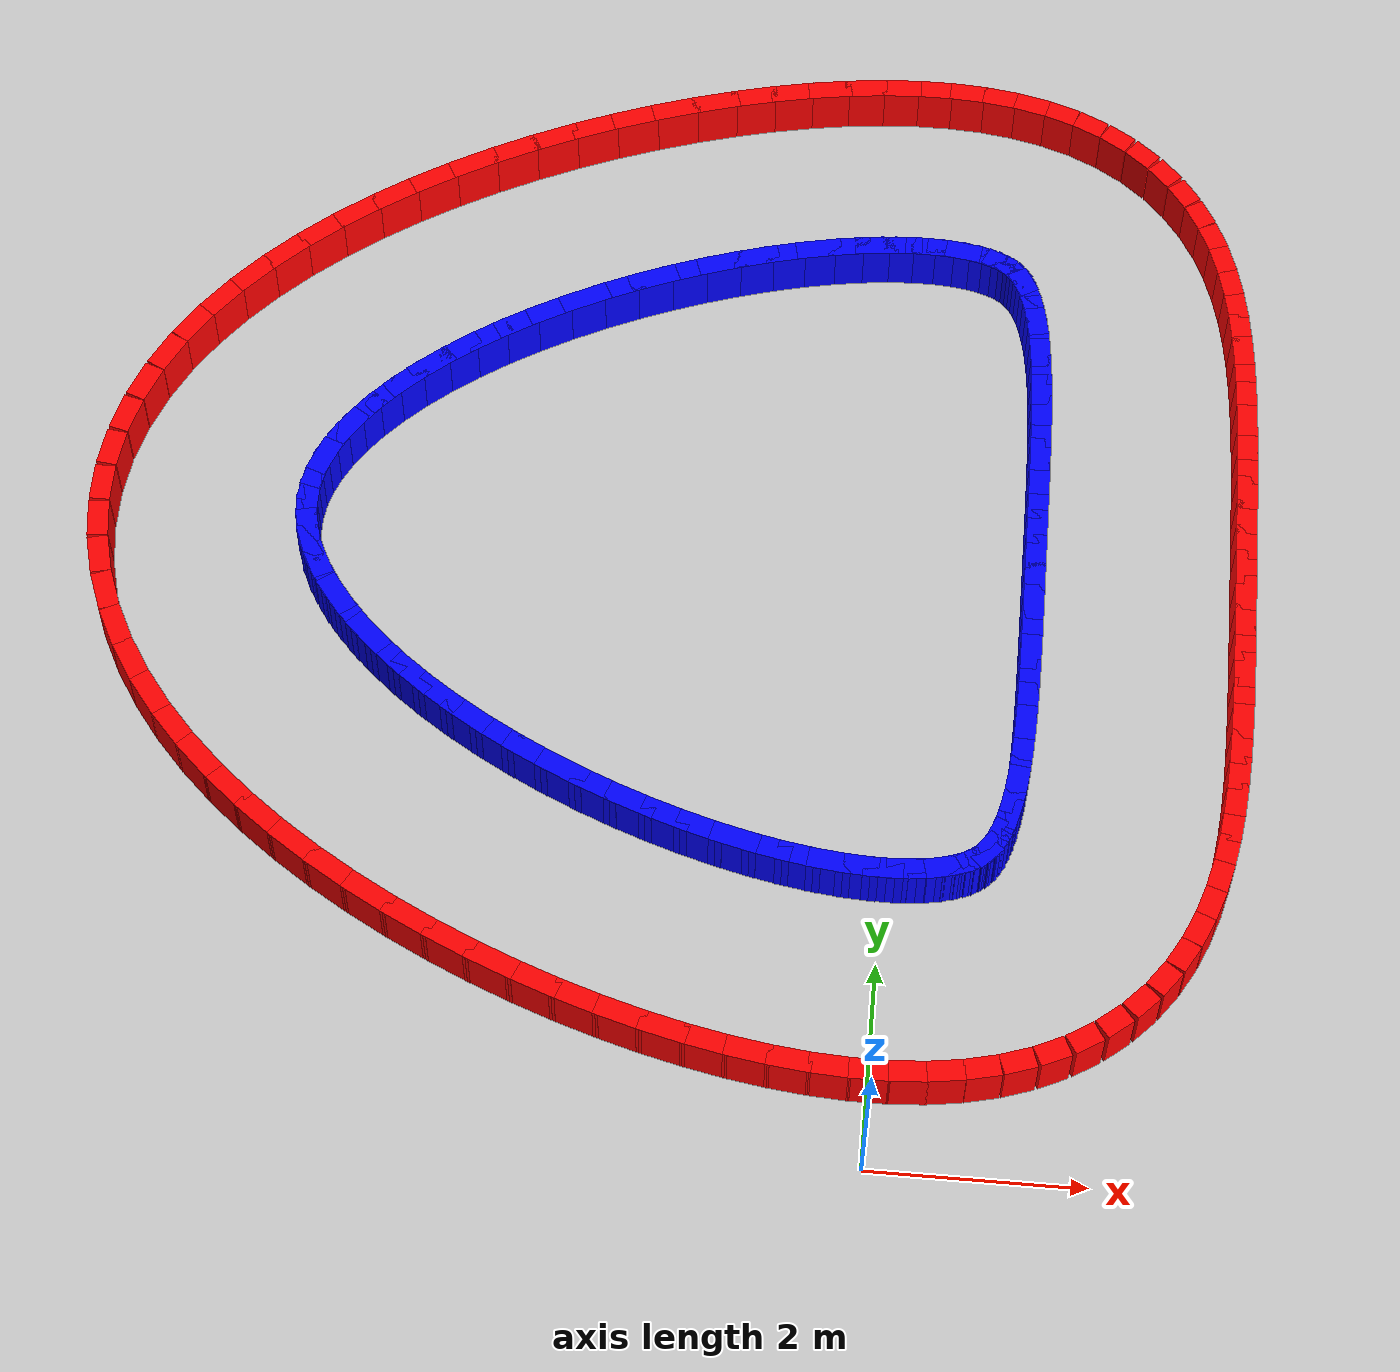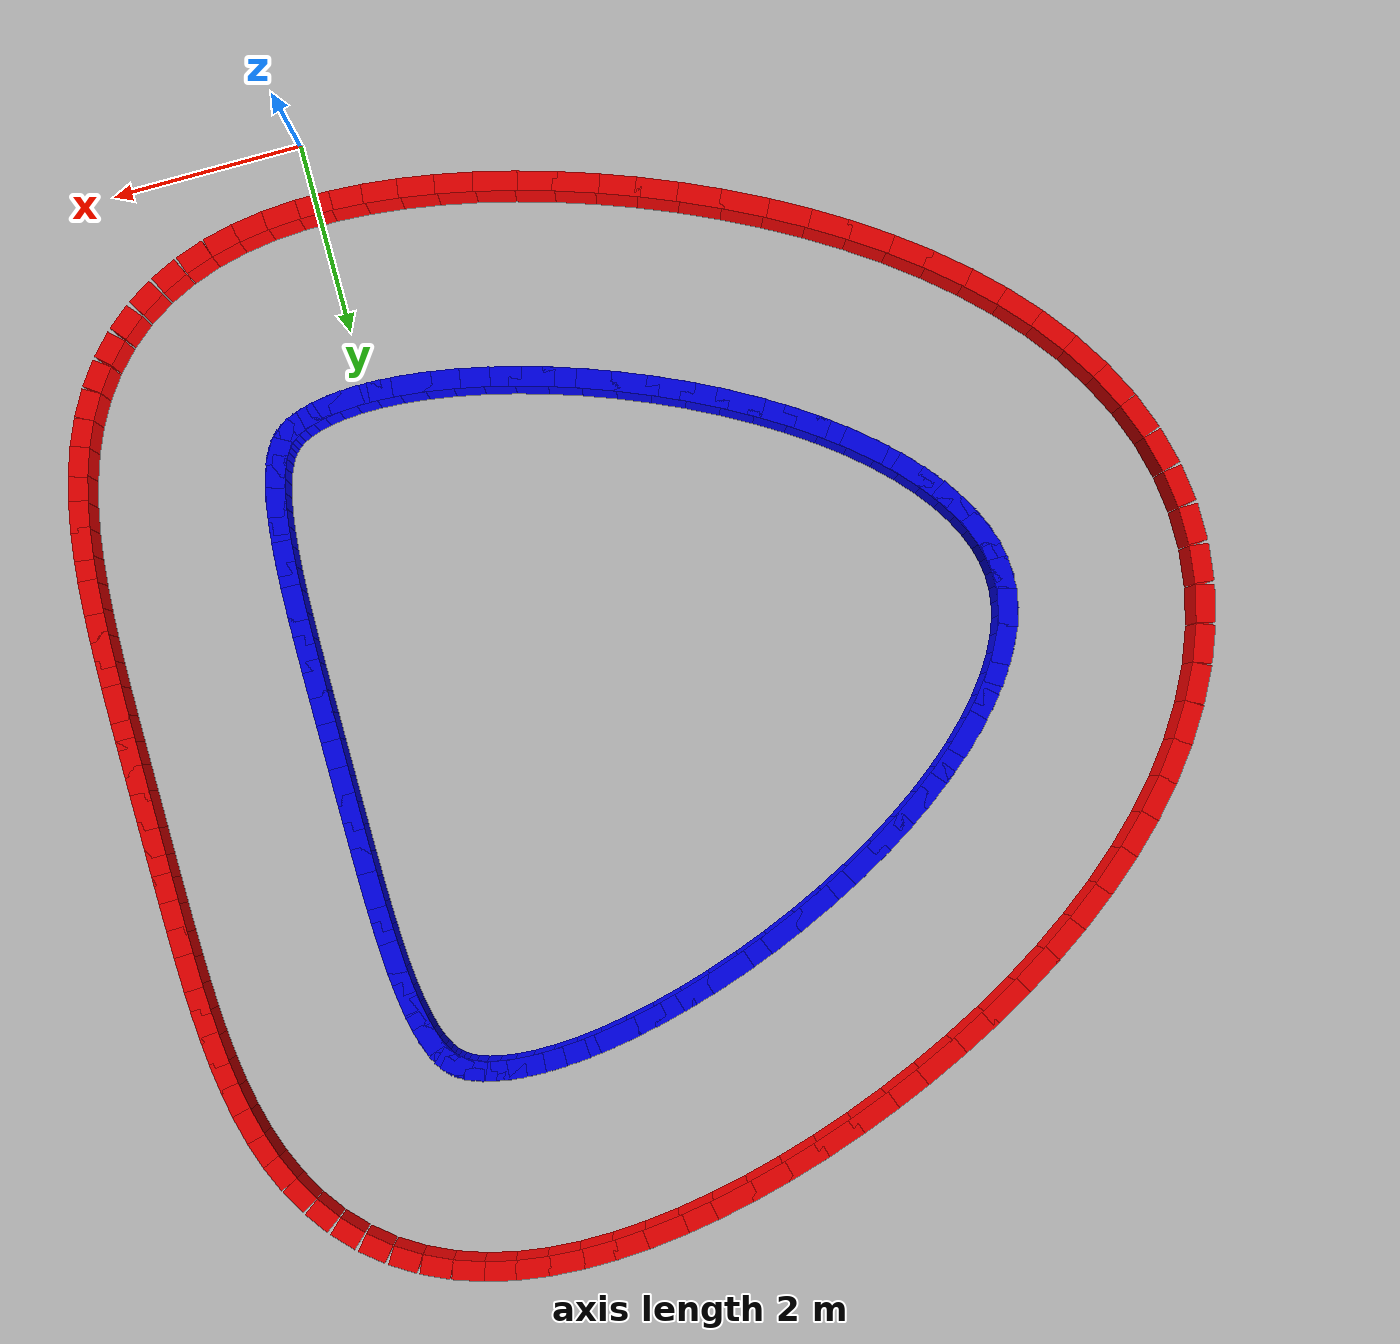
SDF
<?xml version="1.0" ?>
<sdf version="1.9">
  <world name="kidney_track">
    <plugin filename="gz-sim-physics-system" name="gz::sim::systems::Physics"/>
    <plugin filename="gz-sim-user-commands-system" name="gz::sim::systems::UserCommands"/>
    <plugin filename="gz-sim-scene-broadcaster-system" name="gz::sim::systems::SceneBroadcaster"/>
    <plugin filename="gz-sim-sensors-system" name="gz::sim::systems::Sensors">
      <render_engine>ogre2</render_engine>
    </plugin>
    <plugin filename="gz-sim-contact-system" name="gz::sim::systems::Contact"/>

    <light type="directional" name="sun">
      <cast_shadows>true</cast_shadows>
      <pose>0 0 10 0 0 0</pose>
      <diffuse>0.8 0.8 0.8 1</diffuse>
      <specular>0.2 0.2 0.2 1</specular>
      <attenuation><range>1000</range><constant>0.9</constant><linear>0.01</linear><quadratic>0.001</quadratic></attenuation>
      <direction>-0.5 0.1 -0.9</direction>
    </light>

    <model name="ground_plane">
      <static>true</static>
      <link name="link">
        <collision name="collision"><geometry><plane><normal>0 0 1</normal><size>100 100</size></plane></geometry></collision>
        <visual name="visual">
          <geometry><plane><normal>0 0 1</normal><size>100 100</size></plane></geometry>
          <material><ambient>0.8 0.8 0.8 1</ambient><diffuse>0.8 0.8 0.8 1</diffuse></material>
        </visual>
      </link>
    </model>

    <model name="track">
      <static>true</static>

      <!-- Segment 0 -->
      <link name="outer_0">
        <pose>3.2500 6.2500 0.25 0 0 1.5708</pose>
        <collision name="col"><geometry><box><size>0.3826 0.2 0.5</size></box></geometry></collision>
        <visual name="vis"><geometry><box><size>0.3826 0.2 0.5</size></box></geometry><material><ambient>1 0 0 1</ambient></material></visual>
      </link>
      <link name="inner_0">
        <pose>1.2500 6.2500 0.25 0 0 1.5708</pose>
        <collision name="col"><geometry><box><size>0.3826 0.2 0.5</size></box></geometry></collision>
        <visual name="vis"><geometry><box><size>0.3826 0.2 0.5</size></box></geometry><material><ambient>0 0 1 1</ambient></material></visual>
      </link>

      <!-- Segment 1 -->
      <link name="outer_1">
        <pose>3.2500 6.5327 0.25 0 0 1.5709</pose>
        <collision name="col"><geometry><box><size>0.3814 0.2 0.5</size></box></geometry></collision>
        <visual name="vis"><geometry><box><size>0.3814 0.2 0.5</size></box></geometry><material><ambient>1 0 0 1</ambient></material></visual>
      </link>
      <link name="inner_1">
        <pose>1.2500 6.5324 0.25 0 0 1.5709</pose>
        <collision name="col"><geometry><box><size>0.3814 0.2 0.5</size></box></geometry></collision>
        <visual name="vis"><geometry><box><size>0.3814 0.2 0.5</size></box></geometry><material><ambient>0 0 1 1</ambient></material></visual>
      </link>

      <!-- Segment 2 -->
      <link name="outer_2">
        <pose>3.2499 6.8150 0.25 0 0 1.5718</pose>
        <collision name="col"><geometry><box><size>0.3792 0.2 0.5</size></box></geometry></collision>
        <visual name="vis"><geometry><box><size>0.3792 0.2 0.5</size></box></geometry><material><ambient>1 0 0 1</ambient></material></visual>
      </link>
      <link name="inner_2">
        <pose>1.2499 6.8130 0.25 0 0 1.5718</pose>
        <collision name="col"><geometry><box><size>0.3792 0.2 0.5</size></box></geometry></collision>
        <visual name="vis"><geometry><box><size>0.3792 0.2 0.5</size></box></geometry><material><ambient>0 0 1 1</ambient></material></visual>
      </link>

      <!-- Segment 3 -->
      <link name="outer_3">
        <pose>3.2493 7.0966 0.25 0 0 1.5742</pose>
        <collision name="col"><geometry><box><size>0.3759 0.2 0.5</size></box></geometry></collision>
        <visual name="vis"><geometry><box><size>0.3759 0.2 0.5</size></box></geometry><material><ambient>1 0 0 1</ambient></material></visual>
      </link>
      <link name="inner_3">
        <pose>1.2493 7.0898 0.25 0 0 1.5742</pose>
        <collision name="col"><geometry><box><size>0.3759 0.2 0.5</size></box></geometry></collision>
        <visual name="vis"><geometry><box><size>0.3759 0.2 0.5</size></box></geometry><material><ambient>0 0 1 1</ambient></material></visual>
      </link>

      <!-- Segment 4 -->
      <link name="outer_4">
        <pose>3.2477 7.3772 0.25 0 0 1.5789</pose>
        <collision name="col"><geometry><box><size>0.3715 0.2 0.5</size></box></geometry></collision>
        <visual name="vis"><geometry><box><size>0.3715 0.2 0.5</size></box></geometry><material><ambient>1 0 0 1</ambient></material></visual>
      </link>
      <link name="inner_4">
        <pose>1.2478 7.3610 0.25 0 0 1.5789</pose>
        <collision name="col"><geometry><box><size>0.3715 0.2 0.5</size></box></geometry></collision>
        <visual name="vis"><geometry><box><size>0.3715 0.2 0.5</size></box></geometry><material><ambient>0 0 1 1</ambient></material></visual>
      </link>

      <!-- Segment 5 -->
      <link name="outer_5">
        <pose>3.2445 7.6565 0.25 0 0 1.5867</pose>
        <collision name="col"><geometry><box><size>0.3660 0.2 0.5</size></box></geometry></collision>
        <visual name="vis"><geometry><box><size>0.3660 0.2 0.5</size></box></geometry><material><ambient>1 0 0 1</ambient></material></visual>
      </link>
      <link name="inner_5">
        <pose>1.2447 7.6247 0.25 0 0 1.5867</pose>
        <collision name="col"><geometry><box><size>0.3660 0.2 0.5</size></box></geometry></collision>
        <visual name="vis"><geometry><box><size>0.3660 0.2 0.5</size></box></geometry><material><ambient>0 0 1 1</ambient></material></visual>
      </link>

      <!-- Segment 6 -->
      <link name="outer_6">
        <pose>3.2385 7.9344 0.25 0 0 1.5986</pose>
        <collision name="col"><geometry><box><size>0.3596 0.2 0.5</size></box></geometry></collision>
        <visual name="vis"><geometry><box><size>0.3596 0.2 0.5</size></box></geometry><material><ambient>1 0 0 1</ambient></material></visual>
      </link>
      <link name="inner_6">
        <pose>1.2393 7.8787 0.25 0 0 1.5986</pose>
        <collision name="col"><geometry><box><size>0.3596 0.2 0.5</size></box></geometry></collision>
        <visual name="vis"><geometry><box><size>0.3596 0.2 0.5</size></box></geometry><material><ambient>0 0 1 1</ambient></material></visual>
      </link>

      <!-- Segment 7 -->
      <link name="outer_7">
        <pose>3.2286 8.2108 0.25 0 0 1.6156</pose>
        <collision name="col"><geometry><box><size>0.3523 0.2 0.5</size></box></geometry></collision>
        <visual name="vis"><geometry><box><size>0.3523 0.2 0.5</size></box></geometry><material><ambient>1 0 0 1</ambient></material></visual>
      </link>
      <link name="inner_7">
        <pose>1.2306 8.1212 0.25 0 0 1.6156</pose>
        <collision name="col"><geometry><box><size>0.3523 0.2 0.5</size></box></geometry></collision>
        <visual name="vis"><geometry><box><size>0.3523 0.2 0.5</size></box></geometry><material><ambient>0 0 1 1</ambient></material></visual>
      </link>

      <!-- Segment 8 -->
      <link name="outer_8">
        <pose>3.2133 8.4858 0.25 0 0 1.6387</pose>
        <collision name="col"><geometry><box><size>0.3442 0.2 0.5</size></box></geometry></collision>
        <visual name="vis"><geometry><box><size>0.3442 0.2 0.5</size></box></geometry><material><ambient>1 0 0 1</ambient></material></visual>
      </link>
      <link name="inner_8">
        <pose>1.2179 8.3500 0.25 0 0 1.6387</pose>
        <collision name="col"><geometry><box><size>0.3442 0.2 0.5</size></box></geometry></collision>
        <visual name="vis"><geometry><box><size>0.3442 0.2 0.5</size></box></geometry><material><ambient>0 0 1 1</ambient></material></visual>
      </link>

      <!-- Segment 9 -->
      <link name="outer_9">
        <pose>3.1906 8.7596 0.25 0 0 1.6693</pose>
        <collision name="col"><geometry><box><size>0.3354 0.2 0.5</size></box></geometry></collision>
        <visual name="vis"><geometry><box><size>0.3354 0.2 0.5</size></box></geometry><material><ambient>1 0 0 1</ambient></material></visual>
      </link>
      <link name="inner_9">
        <pose>1.2003 8.5629 0.25 0 0 1.6693</pose>
        <collision name="col"><geometry><box><size>0.3354 0.2 0.5</size></box></geometry></collision>
        <visual name="vis"><geometry><box><size>0.3354 0.2 0.5</size></box></geometry><material><ambient>0 0 1 1</ambient></material></visual>
      </link>

      <!-- Segment 10 -->
      <link name="outer_10">
        <pose>3.1584 9.0325 0.25 0 0 1.7087</pose>
        <collision name="col"><geometry><box><size>0.3263 0.2 0.5</size></box></geometry></collision>
        <visual name="vis"><geometry><box><size>0.3263 0.2 0.5</size></box></geometry><material><ambient>1 0 0 1</ambient></material></visual>
      </link>
      <link name="inner_10">
        <pose>1.1774 8.7576 0.25 0 0 1.7087</pose>
        <collision name="col"><geometry><box><size>0.3263 0.2 0.5</size></box></geometry></collision>
        <visual name="vis"><geometry><box><size>0.3263 0.2 0.5</size></box></geometry><material><ambient>0 0 1 1</ambient></material></visual>
      </link>

      <!-- Segment 11 -->
      <link name="outer_11">
        <pose>3.1140 9.3050 0.25 0 0 1.7584</pose>
        <collision name="col"><geometry><box><size>0.3172 0.2 0.5</size></box></geometry></collision>
        <visual name="vis"><geometry><box><size>0.3172 0.2 0.5</size></box></geometry><material><ambient>1 0 0 1</ambient></material></visual>
      </link>
      <link name="inner_11">
        <pose>1.1491 8.9319 0.25 0 0 1.7584</pose>
        <collision name="col"><geometry><box><size>0.3172 0.2 0.5</size></box></geometry></collision>
        <visual name="vis"><geometry><box><size>0.3172 0.2 0.5</size></box></geometry><material><ambient>0 0 1 1</ambient></material></visual>
      </link>

      <!-- Segment 12 -->
      <link name="outer_12">
        <pose>3.0538 9.5771 0.25 0 0 1.8201</pose>
        <collision name="col"><geometry><box><size>0.3083 0.2 0.5</size></box></geometry></collision>
        <visual name="vis"><geometry><box><size>0.3083 0.2 0.5</size></box></geometry><material><ambient>1 0 0 1</ambient></material></visual>
      </link>
      <link name="inner_12">
        <pose>1.1156 9.0838 0.25 0 0 1.8201</pose>
        <collision name="col"><geometry><box><size>0.3083 0.2 0.5</size></box></geometry></collision>
        <visual name="vis"><geometry><box><size>0.3083 0.2 0.5</size></box></geometry><material><ambient>0 0 1 1</ambient></material></visual>
      </link>

      <!-- Segment 13 -->
      <link name="outer_13">
        <pose>2.9740 9.8488 0.25 0 0 1.8949</pose>
        <collision name="col"><geometry><box><size>0.3003 0.2 0.5</size></box></geometry></collision>
        <visual name="vis"><geometry><box><size>0.3003 0.2 0.5</size></box></geometry><material><ambient>1 0 0 1</ambient></material></visual>
      </link>
      <link name="inner_13">
        <pose>1.0782 9.2119 0.25 0 0 1.8949</pose>
        <collision name="col"><geometry><box><size>0.3003 0.2 0.5</size></box></geometry></collision>
        <visual name="vis"><geometry><box><size>0.3003 0.2 0.5</size></box></geometry><material><ambient>0 0 1 1</ambient></material></visual>
      </link>

      <!-- Segment 14 -->
      <link name="outer_14">
        <pose>2.8701 10.1188 0.25 0 0 1.9839</pose>
        <collision name="col"><geometry><box><size>0.2937 0.2 0.5</size></box></geometry></collision>
        <visual name="vis"><geometry><box><size>0.2937 0.2 0.5</size></box></geometry><material><ambient>1 0 0 1</ambient></material></visual>
      </link>
      <link name="inner_14">
        <pose>1.0383 9.3159 0.25 0 0 1.9839</pose>
        <collision name="col"><geometry><box><size>0.2937 0.2 0.5</size></box></geometry></collision>
        <visual name="vis"><geometry><box><size>0.2937 0.2 0.5</size></box></geometry><material><ambient>0 0 1 1</ambient></material></visual>
      </link>

      <!-- Segment 15 -->
      <link name="outer_15">
        <pose>2.7374 10.3841 0.25 0 0 2.0869</pose>
        <collision name="col"><geometry><box><size>0.2891 0.2 0.5</size></box></geometry></collision>
        <visual name="vis"><geometry><box><size>0.2891 0.2 0.5</size></box></geometry><material><ambient>1 0 0 1</ambient></material></visual>
      </link>
      <link name="inner_15">
        <pose>0.9979 9.3971 0.25 0 0 2.0869</pose>
        <collision name="col"><geometry><box><size>0.2891 0.2 0.5</size></box></geometry></collision>
        <visual name="vis"><geometry><box><size>0.2891 0.2 0.5</size></box></geometry><material><ambient>0 0 1 1</ambient></material></visual>
      </link>

      <!-- Segment 16 -->
      <link name="outer_16">
        <pose>2.5723 10.6399 0.25 0 0 2.2023</pose>
        <collision name="col"><geometry><box><size>0.2871 0.2 0.5</size></box></geometry></collision>
        <visual name="vis"><geometry><box><size>0.2871 0.2 0.5</size></box></geometry><material><ambient>1 0 0 1</ambient></material></visual>
      </link>
      <link name="inner_16">
        <pose>0.9581 9.4591 0.25 0 0 2.2023</pose>
        <collision name="col"><geometry><box><size>0.2871 0.2 0.5</size></box></geometry></collision>
        <visual name="vis"><geometry><box><size>0.2871 0.2 0.5</size></box></geometry><material><ambient>0 0 1 1</ambient></material></visual>
      </link>

      <!-- Segment 17 -->
      <link name="outer_17">
        <pose>2.3733 10.8793 0.25 0 0 2.3267</pose>
        <collision name="col"><geometry><box><size>0.2882 0.2 0.5</size></box></geometry></collision>
        <visual name="vis"><geometry><box><size>0.2882 0.2 0.5</size></box></geometry><material><ambient>1 0 0 1</ambient></material></visual>
      </link>
      <link name="inner_17">
        <pose>0.9181 9.5074 0.25 0 0 2.3267</pose>
        <collision name="col"><geometry><box><size>0.2882 0.2 0.5</size></box></geometry></collision>
        <visual name="vis"><geometry><box><size>0.2882 0.2 0.5</size></box></geometry><material><ambient>0 0 1 1</ambient></material></visual>
      </link>

      <!-- Segment 18 -->
      <link name="outer_18">
        <pose>2.1419 11.0952 0.25 0 0 2.4551</pose>
        <collision name="col"><geometry><box><size>0.2926 0.2 0.5</size></box></geometry></collision>
        <visual name="vis"><geometry><box><size>0.2926 0.2 0.5</size></box></geometry><material><ambient>1 0 0 1</ambient></material></visual>
      </link>
      <link name="inner_18">
        <pose>0.8743 9.5482 0.25 0 0 2.4551</pose>
        <collision name="col"><geometry><box><size>0.2926 0.2 0.5</size></box></geometry></collision>
        <visual name="vis"><geometry><box><size>0.2926 0.2 0.5</size></box></geometry><material><ambient>0 0 1 1</ambient></material></visual>
      </link>

      <!-- Segment 19 -->
      <link name="outer_19">
        <pose>1.8826 11.2814 0.25 0 0 2.5819</pose>
        <collision name="col"><geometry><box><size>0.3003 0.2 0.5</size></box></geometry></collision>
        <visual name="vis"><geometry><box><size>0.3003 0.2 0.5</size></box></geometry><material><ambient>1 0 0 1</ambient></material></visual>
      </link>
      <link name="inner_19">
        <pose>0.8207 9.5866 0.25 0 0 2.5819</pose>
        <collision name="col"><geometry><box><size>0.3003 0.2 0.5</size></box></geometry></collision>
        <visual name="vis"><geometry><box><size>0.3003 0.2 0.5</size></box></geometry><material><ambient>0 0 1 1</ambient></material></visual>
      </link>

      <!-- Segment 20 -->
      <link name="outer_20">
        <pose>1.6012 11.4347 0.25 0 0 2.7021</pose>
        <collision name="col"><geometry><box><size>0.3111 0.2 0.5</size></box></geometry></collision>
        <visual name="vis"><geometry><box><size>0.3111 0.2 0.5</size></box></geometry><material><ambient>1 0 0 1</ambient></material></visual>
      </link>
      <link name="inner_20">
        <pose>0.7502 9.6248 0.25 0 0 2.7021</pose>
        <collision name="col"><geometry><box><size>0.3111 0.2 0.5</size></box></geometry></collision>
        <visual name="vis"><geometry><box><size>0.3111 0.2 0.5</size></box></geometry><material><ambient>0 0 1 1</ambient></material></visual>
      </link>

      <!-- Segment 21 -->
      <link name="outer_21">
        <pose>1.3033 11.5549 0.25 0 0 2.8123</pose>
        <collision name="col"><geometry><box><size>0.3244 0.2 0.5</size></box></geometry></collision>
        <visual name="vis"><geometry><box><size>0.3244 0.2 0.5</size></box></geometry><material><ambient>1 0 0 1</ambient></material></visual>
      </link>
      <link name="inner_21">
        <pose>0.6566 9.6624 0.25 0 0 2.8123</pose>
        <collision name="col"><geometry><box><size>0.3244 0.2 0.5</size></box></geometry></collision>
        <visual name="vis"><geometry><box><size>0.3244 0.2 0.5</size></box></geometry><material><ambient>0 0 1 1</ambient></material></visual>
      </link>

      <!-- Segment 22 -->
      <link name="outer_22">
        <pose>0.9927 11.6438 0.25 0 0 2.9110</pose>
        <collision name="col"><geometry><box><size>0.3397 0.2 0.5</size></box></geometry></collision>
        <visual name="vis"><geometry><box><size>0.3397 0.2 0.5</size></box></geometry><material><ambient>1 0 0 1</ambient></material></visual>
      </link>
      <link name="inner_22">
        <pose>0.5357 9.6968 0.25 0 0 2.9110</pose>
        <collision name="col"><geometry><box><size>0.3397 0.2 0.5</size></box></geometry></collision>
        <visual name="vis"><geometry><box><size>0.3397 0.2 0.5</size></box></geometry><material><ambient>0 0 1 1</ambient></material></visual>
      </link>

      <!-- Segment 23 -->
      <link name="outer_23">
        <pose>0.6716 11.7042 0.25 0 0 2.9982</pose>
        <collision name="col"><geometry><box><size>0.3564 0.2 0.5</size></box></geometry></collision>
        <visual name="vis"><geometry><box><size>0.3564 0.2 0.5</size></box></geometry><material><ambient>1 0 0 1</ambient></material></visual>
      </link>
      <link name="inner_23">
        <pose>0.3857 9.7248 0.25 0 0 2.9982</pose>
        <collision name="col"><geometry><box><size>0.3564 0.2 0.5</size></box></geometry></collision>
        <visual name="vis"><geometry><box><size>0.3564 0.2 0.5</size></box></geometry><material><ambient>0 0 1 1</ambient></material></visual>
      </link>

      <!-- Segment 24 -->
      <link name="outer_24">
        <pose>0.3407 11.7389 0.25 0 0 3.0746</pose>
        <collision name="col"><geometry><box><size>0.3738 0.2 0.5</size></box></geometry></collision>
        <visual name="vis"><geometry><box><size>0.3738 0.2 0.5</size></box></geometry><material><ambient>1 0 0 1</ambient></material></visual>
      </link>
      <link name="inner_24">
        <pose>0.2067 9.7434 0.25 0 0 3.0746</pose>
        <collision name="col"><geometry><box><size>0.3738 0.2 0.5</size></box></geometry></collision>
        <visual name="vis"><geometry><box><size>0.3738 0.2 0.5</size></box></geometry><material><ambient>0 0 1 1</ambient></material></visual>
      </link>

      <!-- Segment 25 -->
      <link name="outer_25">
        <pose>0.0000 11.7500 0.25 0 0 3.1416</pose>
        <collision name="col"><geometry><box><size>0.3916 0.2 0.5</size></box></geometry></collision>
        <visual name="vis"><geometry><box><size>0.3916 0.2 0.5</size></box></geometry><material><ambient>1 0 0 1</ambient></material></visual>
      </link>
      <link name="inner_25">
        <pose>0.0000 9.7500 0.25 0 0 3.1416</pose>
        <collision name="col"><geometry><box><size>0.3916 0.2 0.5</size></box></geometry></collision>
        <visual name="vis"><geometry><box><size>0.3916 0.2 0.5</size></box></geometry><material><ambient>0 0 1 1</ambient></material></visual>
      </link>

      <!-- Segment 26 -->
      <link name="outer_26">
        <pose>-0.3505 11.7394 0.25 0 0 -3.0825</pose>
        <collision name="col"><geometry><box><size>0.4091 0.2 0.5</size></box></geometry></collision>
        <visual name="vis"><geometry><box><size>0.4091 0.2 0.5</size></box></geometry><material><ambient>1 0 0 1</ambient></material></visual>
      </link>
      <link name="inner_26">
        <pose>-0.2323 9.7429 0.25 0 0 -3.0825</pose>
        <collision name="col"><geometry><box><size>0.4091 0.2 0.5</size></box></geometry></collision>
        <visual name="vis"><geometry><box><size>0.4091 0.2 0.5</size></box></geometry><material><ambient>0 0 1 1</ambient></material></visual>
      </link>

      <!-- Segment 27 -->
      <link name="outer_27">
        <pose>-0.7109 11.7083 0.25 0 0 -3.0298</pose>
        <collision name="col"><geometry><box><size>0.4259 0.2 0.5</size></box></geometry></collision>
        <visual name="vis"><geometry><box><size>0.4259 0.2 0.5</size></box></geometry><material><ambient>1 0 0 1</ambient></material></visual>
      </link>
      <link name="inner_27">
        <pose>-0.4878 9.7208 0.25 0 0 -3.0298</pose>
        <collision name="col"><geometry><box><size>0.4259 0.2 0.5</size></box></geometry></collision>
        <visual name="vis"><geometry><box><size>0.4259 0.2 0.5</size></box></geometry><material><ambient>0 0 1 1</ambient></material></visual>
      </link>

      <!-- Segment 28 -->
      <link name="outer_28">
        <pose>-1.0808 11.6576 0.25 0 0 -2.9823</pose>
        <collision name="col"><geometry><box><size>0.4417 0.2 0.5</size></box></geometry></collision>
        <visual name="vis"><geometry><box><size>0.4417 0.2 0.5</size></box></geometry><material><ambient>1 0 0 1</ambient></material></visual>
      </link>
      <link name="inner_28">
        <pose>-0.7636 9.6830 0.25 0 0 -2.9823</pose>
        <collision name="col"><geometry><box><size>0.4417 0.2 0.5</size></box></geometry></collision>
        <visual name="vis"><geometry><box><size>0.4417 0.2 0.5</size></box></geometry><material><ambient>0 0 1 1</ambient></material></visual>
      </link>

      <!-- Segment 29 -->
      <link name="outer_29">
        <pose>-1.4597 11.5881 0.25 0 0 -2.9388</pose>
        <collision name="col"><geometry><box><size>0.4560 0.2 0.5</size></box></geometry></collision>
        <visual name="vis"><geometry><box><size>0.4560 0.2 0.5</size></box></geometry><material><ambient>1 0 0 1</ambient></material></visual>
      </link>
      <link name="inner_29">
        <pose>-1.0569 9.6291 0.25 0 0 -2.9388</pose>
        <collision name="col"><geometry><box><size>0.4560 0.2 0.5</size></box></geometry></collision>
        <visual name="vis"><geometry><box><size>0.4560 0.2 0.5</size></box></geometry><material><ambient>0 0 1 1</ambient></material></visual>
      </link>

      <!-- Segment 30 -->
      <link name="outer_30">
        <pose>-1.8463 11.5003 0.25 0 0 -2.8983</pose>
        <collision name="col"><geometry><box><size>0.4687 0.2 0.5</size></box></geometry></collision>
        <visual name="vis"><geometry><box><size>0.4687 0.2 0.5</size></box></geometry><material><ambient>1 0 0 1</ambient></material></visual>
      </link>
      <link name="inner_30">
        <pose>-1.3645 9.5592 0.25 0 0 -2.8983</pose>
        <collision name="col"><geometry><box><size>0.4687 0.2 0.5</size></box></geometry></collision>
        <visual name="vis"><geometry><box><size>0.4687 0.2 0.5</size></box></geometry><material><ambient>0 0 1 1</ambient></material></visual>
      </link>

      <!-- Segment 31 -->
      <link name="outer_31">
        <pose>-2.2395 11.3946 0.25 0 0 -2.8599</pose>
        <collision name="col"><geometry><box><size>0.4794 0.2 0.5</size></box></geometry></collision>
        <visual name="vis"><geometry><box><size>0.4794 0.2 0.5</size></box></geometry><material><ambient>1 0 0 1</ambient></material></visual>
      </link>
      <link name="inner_31">
        <pose>-1.6835 9.4734 0.25 0 0 -2.8599</pose>
        <collision name="col"><geometry><box><size>0.4794 0.2 0.5</size></box></geometry></collision>
        <visual name="vis"><geometry><box><size>0.4794 0.2 0.5</size></box></geometry><material><ambient>0 0 1 1</ambient></material></visual>
      </link>

      <!-- Segment 32 -->
      <link name="outer_32">
        <pose>-2.6373 11.2713 0.25 0 0 -2.8228</pose>
        <collision name="col"><geometry><box><size>0.4880 0.2 0.5</size></box></geometry></collision>
        <visual name="vis"><geometry><box><size>0.4880 0.2 0.5</size></box></geometry><material><ambient>1 0 0 1</ambient></material></visual>
      </link>
      <link name="inner_32">
        <pose>-2.0105 9.3721 0.25 0 0 -2.8228</pose>
        <collision name="col"><geometry><box><size>0.4880 0.2 0.5</size></box></geometry></collision>
        <visual name="vis"><geometry><box><size>0.4880 0.2 0.5</size></box></geometry><material><ambient>0 0 1 1</ambient></material></visual>
      </link>

      <!-- Segment 33 -->
      <link name="outer_33">
        <pose>-3.0379 11.1309 0.25 0 0 -2.7863</pose>
        <collision name="col"><geometry><box><size>0.4943 0.2 0.5</size></box></geometry></collision>
        <visual name="vis"><geometry><box><size>0.4943 0.2 0.5</size></box></geometry><material><ambient>1 0 0 1</ambient></material></visual>
      </link>
      <link name="inner_33">
        <pose>-2.3422 9.2558 0.25 0 0 -2.7863</pose>
        <collision name="col"><geometry><box><size>0.4943 0.2 0.5</size></box></geometry></collision>
        <visual name="vis"><geometry><box><size>0.4943 0.2 0.5</size></box></geometry><material><ambient>0 0 1 1</ambient></material></visual>
      </link>

      <!-- Segment 34 -->
      <link name="outer_34">
        <pose>-3.4391 10.9737 0.25 0 0 -2.7497</pose>
        <collision name="col"><geometry><box><size>0.4982 0.2 0.5</size></box></geometry></collision>
        <visual name="vis"><geometry><box><size>0.4982 0.2 0.5</size></box></geometry><material><ambient>1 0 0 1</ambient></material></visual>
      </link>
      <link name="inner_34">
        <pose>-2.6753 9.1253 0.25 0 0 -2.7497</pose>
        <collision name="col"><geometry><box><size>0.4982 0.2 0.5</size></box></geometry></collision>
        <visual name="vis"><geometry><box><size>0.4982 0.2 0.5</size></box></geometry><material><ambient>0 0 1 1</ambient></material></visual>
      </link>

      <!-- Segment 35 -->
      <link name="outer_35">
        <pose>-3.8385 10.7999 0.25 0 0 -2.7124</pose>
        <collision name="col"><geometry><box><size>0.4997 0.2 0.5</size></box></geometry></collision>
        <visual name="vis"><geometry><box><size>0.4997 0.2 0.5</size></box></geometry><material><ambient>1 0 0 1</ambient></material></visual>
      </link>
      <link name="inner_35">
        <pose>-3.0063 8.9813 0.25 0 0 -2.7124</pose>
        <collision name="col"><geometry><box><size>0.4997 0.2 0.5</size></box></geometry></collision>
        <visual name="vis"><geometry><box><size>0.4997 0.2 0.5</size></box></geometry><material><ambient>0 0 1 1</ambient></material></visual>
      </link>

      <!-- Segment 36 -->
      <link name="outer_36">
        <pose>-4.2336 10.6099 0.25 0 0 -2.6738</pose>
        <collision name="col"><geometry><box><size>0.4988 0.2 0.5</size></box></geometry></collision>
        <visual name="vis"><geometry><box><size>0.4988 0.2 0.5</size></box></geometry><material><ambient>1 0 0 1</ambient></material></visual>
      </link>
      <link name="inner_36">
        <pose>-3.3317 8.8248 0.25 0 0 -2.6738</pose>
        <collision name="col"><geometry><box><size>0.4988 0.2 0.5</size></box></geometry></collision>
        <visual name="vis"><geometry><box><size>0.4988 0.2 0.5</size></box></geometry><material><ambient>0 0 1 1</ambient></material></visual>
      </link>

      <!-- Segment 37 -->
      <link name="outer_37">
        <pose>-4.6217 10.4038 0.25 0 0 -2.6330</pose>
        <collision name="col"><geometry><box><size>0.4954 0.2 0.5</size></box></geometry></collision>
        <visual name="vis"><geometry><box><size>0.4954 0.2 0.5</size></box></geometry><material><ambient>1 0 0 1</ambient></material></visual>
      </link>
      <link name="inner_37">
        <pose>-3.6479 8.6569 0.25 0 0 -2.6330</pose>
        <collision name="col"><geometry><box><size>0.4954 0.2 0.5</size></box></geometry></collision>
        <visual name="vis"><geometry><box><size>0.4954 0.2 0.5</size></box></geometry><material><ambient>0 0 1 1</ambient></material></visual>
      </link>

      <!-- Segment 38 -->
      <link name="outer_38">
        <pose>-5.0004 10.1819 0.25 0 0 -2.5895</pose>
        <collision name="col"><geometry><box><size>0.4898 0.2 0.5</size></box></geometry></collision>
        <visual name="vis"><geometry><box><size>0.4898 0.2 0.5</size></box></geometry><material><ambient>1 0 0 1</ambient></material></visual>
      </link>
      <link name="inner_38">
        <pose>-3.9516 8.4790 0.25 0 0 -2.5895</pose>
        <collision name="col"><geometry><box><size>0.4898 0.2 0.5</size></box></geometry></collision>
        <visual name="vis"><geometry><box><size>0.4898 0.2 0.5</size></box></geometry><material><ambient>0 0 1 1</ambient></material></visual>
      </link>

      <!-- Segment 39 -->
      <link name="outer_39">
        <pose>-5.3670 9.9443 0.25 0 0 -2.5425</pose>
        <collision name="col"><geometry><box><size>0.4822 0.2 0.5</size></box></geometry></collision>
        <visual name="vis"><geometry><box><size>0.4822 0.2 0.5</size></box></geometry><material><ambient>1 0 0 1</ambient></material></visual>
      </link>
      <link name="inner_39">
        <pose>-4.2393 8.2925 0.25 0 0 -2.5425</pose>
        <collision name="col"><geometry><box><size>0.4822 0.2 0.5</size></box></geometry></collision>
        <visual name="vis"><geometry><box><size>0.4822 0.2 0.5</size></box></geometry><material><ambient>0 0 1 1</ambient></material></visual>
      </link>

      <!-- Segment 40 -->
      <link name="outer_40">
        <pose>-5.7187 9.6909 0.25 0 0 -2.4912</pose>
        <collision name="col"><geometry><box><size>0.4727 0.2 0.5</size></box></geometry></collision>
        <visual name="vis"><geometry><box><size>0.4727 0.2 0.5</size></box></geometry><material><ambient>1 0 0 1</ambient></material></visual>
      </link>
      <link name="inner_40">
        <pose>-4.5077 8.0992 0.25 0 0 -2.4912</pose>
        <collision name="col"><geometry><box><size>0.4727 0.2 0.5</size></box></geometry></collision>
        <visual name="vis"><geometry><box><size>0.4727 0.2 0.5</size></box></geometry><material><ambient>0 0 1 1</ambient></material></visual>
      </link>

      <!-- Segment 41 -->
      <link name="outer_41">
        <pose>-6.0531 9.4215 0.25 0 0 -2.4346</pose>
        <collision name="col"><geometry><box><size>0.4618 0.2 0.5</size></box></geometry></collision>
        <visual name="vis"><geometry><box><size>0.4618 0.2 0.5</size></box></geometry><material><ambient>1 0 0 1</ambient></material></visual>
      </link>
      <link name="inner_41">
        <pose>-4.7539 7.9009 0.25 0 0 -2.4346</pose>
        <collision name="col"><geometry><box><size>0.4618 0.2 0.5</size></box></geometry></collision>
        <visual name="vis"><geometry><box><size>0.4618 0.2 0.5</size></box></geometry><material><ambient>0 0 1 1</ambient></material></visual>
      </link>

      <!-- Segment 42 -->
      <link name="outer_42">
        <pose>-6.3672 9.1359 0.25 0 0 -2.3717</pose>
        <collision name="col"><geometry><box><size>0.4497 0.2 0.5</size></box></geometry></collision>
        <visual name="vis"><geometry><box><size>0.4497 0.2 0.5</size></box></geometry><material><ambient>1 0 0 1</ambient></material></visual>
      </link>
      <link name="inner_42">
        <pose>-4.9751 7.6999 0.25 0 0 -2.3717</pose>
        <collision name="col"><geometry><box><size>0.4497 0.2 0.5</size></box></geometry></collision>
        <visual name="vis"><geometry><box><size>0.4497 0.2 0.5</size></box></geometry><material><ambient>0 0 1 1</ambient></material></visual>
      </link>

      <!-- Segment 43 -->
      <link name="outer_43">
        <pose>-6.6585 8.8335 0.25 0 0 -2.3016</pose>
        <collision name="col"><geometry><box><size>0.4371 0.2 0.5</size></box></geometry></collision>
        <visual name="vis"><geometry><box><size>0.4371 0.2 0.5</size></box></geometry><material><ambient>1 0 0 1</ambient></material></visual>
      </link>
      <link name="inner_43">
        <pose>-5.1692 7.4986 0.25 0 0 -2.3016</pose>
        <collision name="col"><geometry><box><size>0.4371 0.2 0.5</size></box></geometry></collision>
        <visual name="vis"><geometry><box><size>0.4371 0.2 0.5</size></box></geometry><material><ambient>0 0 1 1</ambient></material></visual>
      </link>

      <!-- Segment 44 -->
      <link name="outer_44">
        <pose>-6.9237 8.5137 0.25 0 0 -2.2232</pose>
        <collision name="col"><geometry><box><size>0.4245 0.2 0.5</size></box></geometry></collision>
        <visual name="vis"><geometry><box><size>0.4245 0.2 0.5</size></box></geometry><material><ambient>1 0 0 1</ambient></material></visual>
      </link>
      <link name="inner_44">
        <pose>-5.3345 7.2994 0.25 0 0 -2.2232</pose>
        <collision name="col"><geometry><box><size>0.4245 0.2 0.5</size></box></geometry></collision>
        <visual name="vis"><geometry><box><size>0.4245 0.2 0.5</size></box></geometry><material><ambient>0 0 1 1</ambient></material></visual>
      </link>

      <!-- Segment 45 -->
      <link name="outer_45">
        <pose>-7.1595 8.1760 0.25 0 0 -2.1358</pose>
        <collision name="col"><geometry><box><size>0.4124 0.2 0.5</size></box></geometry></collision>
        <visual name="vis"><geometry><box><size>0.4124 0.2 0.5</size></box></geometry><material><ambient>1 0 0 1</ambient></material></visual>
      </link>
      <link name="inner_45">
        <pose>-5.4703 7.1052 0.25 0 0 -2.1358</pose>
        <collision name="col"><geometry><box><size>0.4124 0.2 0.5</size></box></geometry></collision>
        <visual name="vis"><geometry><box><size>0.4124 0.2 0.5</size></box></geometry><material><ambient>0 0 1 1</ambient></material></visual>
      </link>

      <!-- Segment 46 -->
      <link name="outer_46">
        <pose>-7.3619 7.8202 0.25 0 0 -2.0388</pose>
        <collision name="col"><geometry><box><size>0.4016 0.2 0.5</size></box></geometry></collision>
        <visual name="vis"><geometry><box><size>0.4016 0.2 0.5</size></box></geometry><material><ambient>1 0 0 1</ambient></material></visual>
      </link>
      <link name="inner_46">
        <pose>-5.5770 6.9180 0.25 0 0 -2.0388</pose>
        <collision name="col"><geometry><box><size>0.4016 0.2 0.5</size></box></geometry></collision>
        <visual name="vis"><geometry><box><size>0.4016 0.2 0.5</size></box></geometry><material><ambient>0 0 1 1</ambient></material></visual>
      </link>

      <!-- Segment 47 -->
      <link name="outer_47">
        <pose>-7.5267 7.4469 0.25 0 0 -1.9323</pose>
        <collision name="col"><geometry><box><size>0.3927 0.2 0.5</size></box></geometry></collision>
        <visual name="vis"><geometry><box><size>0.3927 0.2 0.5</size></box></geometry><material><ambient>1 0 0 1</ambient></material></visual>
      </link>
      <link name="inner_47">
        <pose>-5.6559 6.7395 0.25 0 0 -1.9323</pose>
        <collision name="col"><geometry><box><size>0.3927 0.2 0.5</size></box></geometry></collision>
        <visual name="vis"><geometry><box><size>0.3927 0.2 0.5</size></box></geometry><material><ambient>0 0 1 1</ambient></material></visual>
      </link>

      <!-- Segment 48 -->
      <link name="outer_48">
        <pose>-7.6489 7.0580 0.25 0 0 -1.8173</pose>
        <collision name="col"><geometry><box><size>0.3864 0.2 0.5</size></box></geometry></collision>
        <visual name="vis"><geometry><box><size>0.3864 0.2 0.5</size></box></geometry><material><ambient>1 0 0 1</ambient></material></visual>
      </link>
      <link name="inner_48">
        <pose>-5.7094 6.5700 0.25 0 0 -1.8173</pose>
        <collision name="col"><geometry><box><size>0.3864 0.2 0.5</size></box></geometry></collision>
        <visual name="vis"><geometry><box><size>0.3864 0.2 0.5</size></box></geometry><material><ambient>0 0 1 1</ambient></material></visual>
      </link>

      <!-- Segment 49 -->
      <link name="outer_49">
        <pose>-7.7244 6.6573 0.25 0 0 -1.6958</pose>
        <collision name="col"><geometry><box><size>0.3831 0.2 0.5</size></box></geometry></collision>
        <visual name="vis"><geometry><box><size>0.3831 0.2 0.5</size></box></geometry><material><ambient>1 0 0 1</ambient></material></visual>
      </link>
      <link name="inner_49">
        <pose>-5.7401 6.4078 0.25 0 0 -1.6958</pose>
        <collision name="col"><geometry><box><size>0.3831 0.2 0.5</size></box></geometry></collision>
        <visual name="vis"><geometry><box><size>0.3831 0.2 0.5</size></box></geometry><material><ambient>0 0 1 1</ambient></material></visual>
      </link>

      <!-- Segment 50 -->
      <link name="outer_50">
        <pose>-7.7500 6.2500 0.25 0 0 -1.5708</pose>
        <collision name="col"><geometry><box><size>0.3831 0.2 0.5</size></box></geometry></collision>
        <visual name="vis"><geometry><box><size>0.3831 0.2 0.5</size></box></geometry><material><ambient>1 0 0 1</ambient></material></visual>
      </link>
      <link name="inner_50">
        <pose>-5.7500 6.2500 0.25 0 0 -1.5708</pose>
        <collision name="col"><geometry><box><size>0.3831 0.2 0.5</size></box></geometry></collision>
        <visual name="vis"><geometry><box><size>0.3831 0.2 0.5</size></box></geometry><material><ambient>0 0 1 1</ambient></material></visual>
      </link>

      <!-- Segment 51 -->
      <link name="outer_51">
        <pose>-7.7244 5.8427 0.25 0 0 -1.4458</pose>
        <collision name="col"><geometry><box><size>0.3864 0.2 0.5</size></box></geometry></collision>
        <visual name="vis"><geometry><box><size>0.3864 0.2 0.5</size></box></geometry><material><ambient>1 0 0 1</ambient></material></visual>
      </link>
      <link name="inner_51">
        <pose>-5.7401 6.0922 0.25 0 0 -1.4458</pose>
        <collision name="col"><geometry><box><size>0.3864 0.2 0.5</size></box></geometry></collision>
        <visual name="vis"><geometry><box><size>0.3864 0.2 0.5</size></box></geometry><material><ambient>0 0 1 1</ambient></material></visual>
      </link>

      <!-- Segment 52 -->
      <link name="outer_52">
        <pose>-7.6489 5.4420 0.25 0 0 -1.3243</pose>
        <collision name="col"><geometry><box><size>0.3927 0.2 0.5</size></box></geometry></collision>
        <visual name="vis"><geometry><box><size>0.3927 0.2 0.5</size></box></geometry><material><ambient>1 0 0 1</ambient></material></visual>
      </link>
      <link name="inner_52">
        <pose>-5.7094 5.9300 0.25 0 0 -1.3243</pose>
        <collision name="col"><geometry><box><size>0.3927 0.2 0.5</size></box></geometry></collision>
        <visual name="vis"><geometry><box><size>0.3927 0.2 0.5</size></box></geometry><material><ambient>0 0 1 1</ambient></material></visual>
      </link>

      <!-- Segment 53 -->
      <link name="outer_53">
        <pose>-7.5267 5.0531 0.25 0 0 -1.2093</pose>
        <collision name="col"><geometry><box><size>0.4016 0.2 0.5</size></box></geometry></collision>
        <visual name="vis"><geometry><box><size>0.4016 0.2 0.5</size></box></geometry><material><ambient>1 0 0 1</ambient></material></visual>
      </link>
      <link name="inner_53">
        <pose>-5.6559 5.7605 0.25 0 0 -1.2093</pose>
        <collision name="col"><geometry><box><size>0.4016 0.2 0.5</size></box></geometry></collision>
        <visual name="vis"><geometry><box><size>0.4016 0.2 0.5</size></box></geometry><material><ambient>0 0 1 1</ambient></material></visual>
      </link>

      <!-- Segment 54 -->
      <link name="outer_54">
        <pose>-7.3619 4.6798 0.25 0 0 -1.1028</pose>
        <collision name="col"><geometry><box><size>0.4124 0.2 0.5</size></box></geometry></collision>
        <visual name="vis"><geometry><box><size>0.4124 0.2 0.5</size></box></geometry><material><ambient>1 0 0 1</ambient></material></visual>
      </link>
      <link name="inner_54">
        <pose>-5.5770 5.5820 0.25 0 0 -1.1028</pose>
        <collision name="col"><geometry><box><size>0.4124 0.2 0.5</size></box></geometry></collision>
        <visual name="vis"><geometry><box><size>0.4124 0.2 0.5</size></box></geometry><material><ambient>0 0 1 1</ambient></material></visual>
      </link>

      <!-- Segment 55 -->
      <link name="outer_55">
        <pose>-7.1595 4.3240 0.25 0 0 -1.0058</pose>
        <collision name="col"><geometry><box><size>0.4245 0.2 0.5</size></box></geometry></collision>
        <visual name="vis"><geometry><box><size>0.4245 0.2 0.5</size></box></geometry><material><ambient>1 0 0 1</ambient></material></visual>
      </link>
      <link name="inner_55">
        <pose>-5.4703 5.3948 0.25 0 0 -1.0058</pose>
        <collision name="col"><geometry><box><size>0.4245 0.2 0.5</size></box></geometry></collision>
        <visual name="vis"><geometry><box><size>0.4245 0.2 0.5</size></box></geometry><material><ambient>0 0 1 1</ambient></material></visual>
      </link>

      <!-- Segment 56 -->
      <link name="outer_56">
        <pose>-6.9237 3.9863 0.25 0 0 -0.9184</pose>
        <collision name="col"><geometry><box><size>0.4371 0.2 0.5</size></box></geometry></collision>
        <visual name="vis"><geometry><box><size>0.4371 0.2 0.5</size></box></geometry><material><ambient>1 0 0 1</ambient></material></visual>
      </link>
      <link name="inner_56">
        <pose>-5.3345 5.2006 0.25 0 0 -0.9184</pose>
        <collision name="col"><geometry><box><size>0.4371 0.2 0.5</size></box></geometry></collision>
        <visual name="vis"><geometry><box><size>0.4371 0.2 0.5</size></box></geometry><material><ambient>0 0 1 1</ambient></material></visual>
      </link>

      <!-- Segment 57 -->
      <link name="outer_57">
        <pose>-6.6585 3.6665 0.25 0 0 -0.8400</pose>
        <collision name="col"><geometry><box><size>0.4497 0.2 0.5</size></box></geometry></collision>
        <visual name="vis"><geometry><box><size>0.4497 0.2 0.5</size></box></geometry><material><ambient>1 0 0 1</ambient></material></visual>
      </link>
      <link name="inner_57">
        <pose>-5.1692 5.0014 0.25 0 0 -0.8400</pose>
        <collision name="col"><geometry><box><size>0.4497 0.2 0.5</size></box></geometry></collision>
        <visual name="vis"><geometry><box><size>0.4497 0.2 0.5</size></box></geometry><material><ambient>0 0 1 1</ambient></material></visual>
      </link>

      <!-- Segment 58 -->
      <link name="outer_58">
        <pose>-6.3672 3.3641 0.25 0 0 -0.7699</pose>
        <collision name="col"><geometry><box><size>0.4618 0.2 0.5</size></box></geometry></collision>
        <visual name="vis"><geometry><box><size>0.4618 0.2 0.5</size></box></geometry><material><ambient>1 0 0 1</ambient></material></visual>
      </link>
      <link name="inner_58">
        <pose>-4.9751 4.8001 0.25 0 0 -0.7699</pose>
        <collision name="col"><geometry><box><size>0.4618 0.2 0.5</size></box></geometry></collision>
        <visual name="vis"><geometry><box><size>0.4618 0.2 0.5</size></box></geometry><material><ambient>0 0 1 1</ambient></material></visual>
      </link>

      <!-- Segment 59 -->
      <link name="outer_59">
        <pose>-6.0531 3.0785 0.25 0 0 -0.7070</pose>
        <collision name="col"><geometry><box><size>0.4727 0.2 0.5</size></box></geometry></collision>
        <visual name="vis"><geometry><box><size>0.4727 0.2 0.5</size></box></geometry><material><ambient>1 0 0 1</ambient></material></visual>
      </link>
      <link name="inner_59">
        <pose>-4.7539 4.5991 0.25 0 0 -0.7070</pose>
        <collision name="col"><geometry><box><size>0.4727 0.2 0.5</size></box></geometry></collision>
        <visual name="vis"><geometry><box><size>0.4727 0.2 0.5</size></box></geometry><material><ambient>0 0 1 1</ambient></material></visual>
      </link>

      <!-- Segment 60 -->
      <link name="outer_60">
        <pose>-5.7187 2.8091 0.25 0 0 -0.6504</pose>
        <collision name="col"><geometry><box><size>0.4822 0.2 0.5</size></box></geometry></collision>
        <visual name="vis"><geometry><box><size>0.4822 0.2 0.5</size></box></geometry><material><ambient>1 0 0 1</ambient></material></visual>
      </link>
      <link name="inner_60">
        <pose>-4.5077 4.4008 0.25 0 0 -0.6504</pose>
        <collision name="col"><geometry><box><size>0.4822 0.2 0.5</size></box></geometry></collision>
        <visual name="vis"><geometry><box><size>0.4822 0.2 0.5</size></box></geometry><material><ambient>0 0 1 1</ambient></material></visual>
      </link>

      <!-- Segment 61 -->
      <link name="outer_61">
        <pose>-5.3670 2.5557 0.25 0 0 -0.5991</pose>
        <collision name="col"><geometry><box><size>0.4898 0.2 0.5</size></box></geometry></collision>
        <visual name="vis"><geometry><box><size>0.4898 0.2 0.5</size></box></geometry><material><ambient>1 0 0 1</ambient></material></visual>
      </link>
      <link name="inner_61">
        <pose>-4.2393 4.2075 0.25 0 0 -0.5991</pose>
        <collision name="col"><geometry><box><size>0.4898 0.2 0.5</size></box></geometry></collision>
        <visual name="vis"><geometry><box><size>0.4898 0.2 0.5</size></box></geometry><material><ambient>0 0 1 1</ambient></material></visual>
      </link>

      <!-- Segment 62 -->
      <link name="outer_62">
        <pose>-5.0004 2.3181 0.25 0 0 -0.5520</pose>
        <collision name="col"><geometry><box><size>0.4954 0.2 0.5</size></box></geometry></collision>
        <visual name="vis"><geometry><box><size>0.4954 0.2 0.5</size></box></geometry><material><ambient>1 0 0 1</ambient></material></visual>
      </link>
      <link name="inner_62">
        <pose>-3.9516 4.0210 0.25 0 0 -0.5520</pose>
        <collision name="col"><geometry><box><size>0.4954 0.2 0.5</size></box></geometry></collision>
        <visual name="vis"><geometry><box><size>0.4954 0.2 0.5</size></box></geometry><material><ambient>0 0 1 1</ambient></material></visual>
      </link>

      <!-- Segment 63 -->
      <link name="outer_63">
        <pose>-4.6217 2.0962 0.25 0 0 -0.5086</pose>
        <collision name="col"><geometry><box><size>0.4988 0.2 0.5</size></box></geometry></collision>
        <visual name="vis"><geometry><box><size>0.4988 0.2 0.5</size></box></geometry><material><ambient>1 0 0 1</ambient></material></visual>
      </link>
      <link name="inner_63">
        <pose>-3.6479 3.8431 0.25 0 0 -0.5086</pose>
        <collision name="col"><geometry><box><size>0.4988 0.2 0.5</size></box></geometry></collision>
        <visual name="vis"><geometry><box><size>0.4988 0.2 0.5</size></box></geometry><material><ambient>0 0 1 1</ambient></material></visual>
      </link>

      <!-- Segment 64 -->
      <link name="outer_64">
        <pose>-4.2336 1.8901 0.25 0 0 -0.4678</pose>
        <collision name="col"><geometry><box><size>0.4997 0.2 0.5</size></box></geometry></collision>
        <visual name="vis"><geometry><box><size>0.4997 0.2 0.5</size></box></geometry><material><ambient>1 0 0 1</ambient></material></visual>
      </link>
      <link name="inner_64">
        <pose>-3.3317 3.6752 0.25 0 0 -0.4678</pose>
        <collision name="col"><geometry><box><size>0.4997 0.2 0.5</size></box></geometry></collision>
        <visual name="vis"><geometry><box><size>0.4997 0.2 0.5</size></box></geometry><material><ambient>0 0 1 1</ambient></material></visual>
      </link>

      <!-- Segment 65 -->
      <link name="outer_65">
        <pose>-3.8385 1.7001 0.25 0 0 -0.4291</pose>
        <collision name="col"><geometry><box><size>0.4982 0.2 0.5</size></box></geometry></collision>
        <visual name="vis"><geometry><box><size>0.4982 0.2 0.5</size></box></geometry><material><ambient>1 0 0 1</ambient></material></visual>
      </link>
      <link name="inner_65">
        <pose>-3.0063 3.5187 0.25 0 0 -0.4291</pose>
        <collision name="col"><geometry><box><size>0.4982 0.2 0.5</size></box></geometry></collision>
        <visual name="vis"><geometry><box><size>0.4982 0.2 0.5</size></box></geometry><material><ambient>0 0 1 1</ambient></material></visual>
      </link>

      <!-- Segment 66 -->
      <link name="outer_66">
        <pose>-3.4391 1.5263 0.25 0 0 -0.3918</pose>
        <collision name="col"><geometry><box><size>0.4943 0.2 0.5</size></box></geometry></collision>
        <visual name="vis"><geometry><box><size>0.4943 0.2 0.5</size></box></geometry><material><ambient>1 0 0 1</ambient></material></visual>
      </link>
      <link name="inner_66">
        <pose>-2.6753 3.3747 0.25 0 0 -0.3918</pose>
        <collision name="col"><geometry><box><size>0.4943 0.2 0.5</size></box></geometry></collision>
        <visual name="vis"><geometry><box><size>0.4943 0.2 0.5</size></box></geometry><material><ambient>0 0 1 1</ambient></material></visual>
      </link>

      <!-- Segment 67 -->
      <link name="outer_67">
        <pose>-3.0379 1.3691 0.25 0 0 -0.3553</pose>
        <collision name="col"><geometry><box><size>0.4880 0.2 0.5</size></box></geometry></collision>
        <visual name="vis"><geometry><box><size>0.4880 0.2 0.5</size></box></geometry><material><ambient>1 0 0 1</ambient></material></visual>
      </link>
      <link name="inner_67">
        <pose>-2.3422 3.2442 0.25 0 0 -0.3553</pose>
        <collision name="col"><geometry><box><size>0.4880 0.2 0.5</size></box></geometry></collision>
        <visual name="vis"><geometry><box><size>0.4880 0.2 0.5</size></box></geometry><material><ambient>0 0 1 1</ambient></material></visual>
      </link>

      <!-- Segment 68 -->
      <link name="outer_68">
        <pose>-2.6373 1.2287 0.25 0 0 -0.3188</pose>
        <collision name="col"><geometry><box><size>0.4794 0.2 0.5</size></box></geometry></collision>
        <visual name="vis"><geometry><box><size>0.4794 0.2 0.5</size></box></geometry><material><ambient>1 0 0 1</ambient></material></visual>
      </link>
      <link name="inner_68">
        <pose>-2.0105 3.1279 0.25 0 0 -0.3188</pose>
        <collision name="col"><geometry><box><size>0.4794 0.2 0.5</size></box></geometry></collision>
        <visual name="vis"><geometry><box><size>0.4794 0.2 0.5</size></box></geometry><material><ambient>0 0 1 1</ambient></material></visual>
      </link>

      <!-- Segment 69 -->
      <link name="outer_69">
        <pose>-2.2395 1.1054 0.25 0 0 -0.2817</pose>
        <collision name="col"><geometry><box><size>0.4687 0.2 0.5</size></box></geometry></collision>
        <visual name="vis"><geometry><box><size>0.4687 0.2 0.5</size></box></geometry><material><ambient>1 0 0 1</ambient></material></visual>
      </link>
      <link name="inner_69">
        <pose>-1.6835 3.0266 0.25 0 0 -0.2817</pose>
        <collision name="col"><geometry><box><size>0.4687 0.2 0.5</size></box></geometry></collision>
        <visual name="vis"><geometry><box><size>0.4687 0.2 0.5</size></box></geometry><material><ambient>0 0 1 1</ambient></material></visual>
      </link>

      <!-- Segment 70 -->
      <link name="outer_70">
        <pose>-1.8463 0.9997 0.25 0 0 -0.2433</pose>
        <collision name="col"><geometry><box><size>0.4560 0.2 0.5</size></box></geometry></collision>
        <visual name="vis"><geometry><box><size>0.4560 0.2 0.5</size></box></geometry><material><ambient>1 0 0 1</ambient></material></visual>
      </link>
      <link name="inner_70">
        <pose>-1.3645 2.9408 0.25 0 0 -0.2433</pose>
        <collision name="col"><geometry><box><size>0.4560 0.2 0.5</size></box></geometry></collision>
        <visual name="vis"><geometry><box><size>0.4560 0.2 0.5</size></box></geometry><material><ambient>0 0 1 1</ambient></material></visual>
      </link>

      <!-- Segment 71 -->
      <link name="outer_71">
        <pose>-1.4597 0.9119 0.25 0 0 -0.2028</pose>
        <collision name="col"><geometry><box><size>0.4417 0.2 0.5</size></box></geometry></collision>
        <visual name="vis"><geometry><box><size>0.4417 0.2 0.5</size></box></geometry><material><ambient>1 0 0 1</ambient></material></visual>
      </link>
      <link name="inner_71">
        <pose>-1.0569 2.8709 0.25 0 0 -0.2028</pose>
        <collision name="col"><geometry><box><size>0.4417 0.2 0.5</size></box></geometry></collision>
        <visual name="vis"><geometry><box><size>0.4417 0.2 0.5</size></box></geometry><material><ambient>0 0 1 1</ambient></material></visual>
      </link>

      <!-- Segment 72 -->
      <link name="outer_72">
        <pose>-1.0808 0.8424 0.25 0 0 -0.1593</pose>
        <collision name="col"><geometry><box><size>0.4259 0.2 0.5</size></box></geometry></collision>
        <visual name="vis"><geometry><box><size>0.4259 0.2 0.5</size></box></geometry><material><ambient>1 0 0 1</ambient></material></visual>
      </link>
      <link name="inner_72">
        <pose>-0.7636 2.8170 0.25 0 0 -0.1593</pose>
        <collision name="col"><geometry><box><size>0.4259 0.2 0.5</size></box></geometry></collision>
        <visual name="vis"><geometry><box><size>0.4259 0.2 0.5</size></box></geometry><material><ambient>0 0 1 1</ambient></material></visual>
      </link>

      <!-- Segment 73 -->
      <link name="outer_73">
        <pose>-0.7109 0.7917 0.25 0 0 -0.1118</pose>
        <collision name="col"><geometry><box><size>0.4091 0.2 0.5</size></box></geometry></collision>
        <visual name="vis"><geometry><box><size>0.4091 0.2 0.5</size></box></geometry><material><ambient>1 0 0 1</ambient></material></visual>
      </link>
      <link name="inner_73">
        <pose>-0.4878 2.7792 0.25 0 0 -0.1118</pose>
        <collision name="col"><geometry><box><size>0.4091 0.2 0.5</size></box></geometry></collision>
        <visual name="vis"><geometry><box><size>0.4091 0.2 0.5</size></box></geometry><material><ambient>0 0 1 1</ambient></material></visual>
      </link>

      <!-- Segment 74 -->
      <link name="outer_74">
        <pose>-0.3505 0.7606 0.25 0 0 -0.0591</pose>
        <collision name="col"><geometry><box><size>0.3916 0.2 0.5</size></box></geometry></collision>
        <visual name="vis"><geometry><box><size>0.3916 0.2 0.5</size></box></geometry><material><ambient>1 0 0 1</ambient></material></visual>
      </link>
      <link name="inner_74">
        <pose>-0.2323 2.7571 0.25 0 0 -0.0591</pose>
        <collision name="col"><geometry><box><size>0.3916 0.2 0.5</size></box></geometry></collision>
        <visual name="vis"><geometry><box><size>0.3916 0.2 0.5</size></box></geometry><material><ambient>0 0 1 1</ambient></material></visual>
      </link>

      <!-- Segment 75 -->
      <link name="outer_75">
        <pose>-0.0000 0.7500 0.25 0 0 0.0000</pose>
        <collision name="col"><geometry><box><size>0.3738 0.2 0.5</size></box></geometry></collision>
        <visual name="vis"><geometry><box><size>0.3738 0.2 0.5</size></box></geometry><material><ambient>1 0 0 1</ambient></material></visual>
      </link>
      <link name="inner_75">
        <pose>-0.0000 2.7500 0.25 0 0 0.0000</pose>
        <collision name="col"><geometry><box><size>0.3738 0.2 0.5</size></box></geometry></collision>
        <visual name="vis"><geometry><box><size>0.3738 0.2 0.5</size></box></geometry><material><ambient>0 0 1 1</ambient></material></visual>
      </link>

      <!-- Segment 76 -->
      <link name="outer_76">
        <pose>0.3407 0.7611 0.25 0 0 0.0670</pose>
        <collision name="col"><geometry><box><size>0.3564 0.2 0.5</size></box></geometry></collision>
        <visual name="vis"><geometry><box><size>0.3564 0.2 0.5</size></box></geometry><material><ambient>1 0 0 1</ambient></material></visual>
      </link>
      <link name="inner_76">
        <pose>0.2067 2.7566 0.25 0 0 0.0670</pose>
        <collision name="col"><geometry><box><size>0.3564 0.2 0.5</size></box></geometry></collision>
        <visual name="vis"><geometry><box><size>0.3564 0.2 0.5</size></box></geometry><material><ambient>0 0 1 1</ambient></material></visual>
      </link>

      <!-- Segment 77 -->
      <link name="outer_77">
        <pose>0.6716 0.7958 0.25 0 0 0.1434</pose>
        <collision name="col"><geometry><box><size>0.3397 0.2 0.5</size></box></geometry></collision>
        <visual name="vis"><geometry><box><size>0.3397 0.2 0.5</size></box></geometry><material><ambient>1 0 0 1</ambient></material></visual>
      </link>
      <link name="inner_77">
        <pose>0.3857 2.7752 0.25 0 0 0.1434</pose>
        <collision name="col"><geometry><box><size>0.3397 0.2 0.5</size></box></geometry></collision>
        <visual name="vis"><geometry><box><size>0.3397 0.2 0.5</size></box></geometry><material><ambient>0 0 1 1</ambient></material></visual>
      </link>

      <!-- Segment 78 -->
      <link name="outer_78">
        <pose>0.9927 0.8562 0.25 0 0 0.2306</pose>
        <collision name="col"><geometry><box><size>0.3244 0.2 0.5</size></box></geometry></collision>
        <visual name="vis"><geometry><box><size>0.3244 0.2 0.5</size></box></geometry><material><ambient>1 0 0 1</ambient></material></visual>
      </link>
      <link name="inner_78">
        <pose>0.5357 2.8032 0.25 0 0 0.2306</pose>
        <collision name="col"><geometry><box><size>0.3244 0.2 0.5</size></box></geometry></collision>
        <visual name="vis"><geometry><box><size>0.3244 0.2 0.5</size></box></geometry><material><ambient>0 0 1 1</ambient></material></visual>
      </link>

      <!-- Segment 79 -->
      <link name="outer_79">
        <pose>1.3033 0.9451 0.25 0 0 0.3293</pose>
        <collision name="col"><geometry><box><size>0.3111 0.2 0.5</size></box></geometry></collision>
        <visual name="vis"><geometry><box><size>0.3111 0.2 0.5</size></box></geometry><material><ambient>1 0 0 1</ambient></material></visual>
      </link>
      <link name="inner_79">
        <pose>0.6566 2.8376 0.25 0 0 0.3293</pose>
        <collision name="col"><geometry><box><size>0.3111 0.2 0.5</size></box></geometry></collision>
        <visual name="vis"><geometry><box><size>0.3111 0.2 0.5</size></box></geometry><material><ambient>0 0 1 1</ambient></material></visual>
      </link>

      <!-- Segment 80 -->
      <link name="outer_80">
        <pose>1.6012 1.0653 0.25 0 0 0.4395</pose>
        <collision name="col"><geometry><box><size>0.3003 0.2 0.5</size></box></geometry></collision>
        <visual name="vis"><geometry><box><size>0.3003 0.2 0.5</size></box></geometry><material><ambient>1 0 0 1</ambient></material></visual>
      </link>
      <link name="inner_80">
        <pose>0.7502 2.8752 0.25 0 0 0.4395</pose>
        <collision name="col"><geometry><box><size>0.3003 0.2 0.5</size></box></geometry></collision>
        <visual name="vis"><geometry><box><size>0.3003 0.2 0.5</size></box></geometry><material><ambient>0 0 1 1</ambient></material></visual>
      </link>

      <!-- Segment 81 -->
      <link name="outer_81">
        <pose>1.8826 1.2186 0.25 0 0 0.5597</pose>
        <collision name="col"><geometry><box><size>0.2926 0.2 0.5</size></box></geometry></collision>
        <visual name="vis"><geometry><box><size>0.2926 0.2 0.5</size></box></geometry><material><ambient>1 0 0 1</ambient></material></visual>
      </link>
      <link name="inner_81">
        <pose>0.8207 2.9134 0.25 0 0 0.5597</pose>
        <collision name="col"><geometry><box><size>0.2926 0.2 0.5</size></box></geometry></collision>
        <visual name="vis"><geometry><box><size>0.2926 0.2 0.5</size></box></geometry><material><ambient>0 0 1 1</ambient></material></visual>
      </link>

      <!-- Segment 82 -->
      <link name="outer_82">
        <pose>2.1419 1.4048 0.25 0 0 0.6865</pose>
        <collision name="col"><geometry><box><size>0.2882 0.2 0.5</size></box></geometry></collision>
        <visual name="vis"><geometry><box><size>0.2882 0.2 0.5</size></box></geometry><material><ambient>1 0 0 1</ambient></material></visual>
      </link>
      <link name="inner_82">
        <pose>0.8743 2.9518 0.25 0 0 0.6865</pose>
        <collision name="col"><geometry><box><size>0.2882 0.2 0.5</size></box></geometry></collision>
        <visual name="vis"><geometry><box><size>0.2882 0.2 0.5</size></box></geometry><material><ambient>0 0 1 1</ambient></material></visual>
      </link>

      <!-- Segment 83 -->
      <link name="outer_83">
        <pose>2.3733 1.6207 0.25 0 0 0.8149</pose>
        <collision name="col"><geometry><box><size>0.2871 0.2 0.5</size></box></geometry></collision>
        <visual name="vis"><geometry><box><size>0.2871 0.2 0.5</size></box></geometry><material><ambient>1 0 0 1</ambient></material></visual>
      </link>
      <link name="inner_83">
        <pose>0.9181 2.9926 0.25 0 0 0.8149</pose>
        <collision name="col"><geometry><box><size>0.2871 0.2 0.5</size></box></geometry></collision>
        <visual name="vis"><geometry><box><size>0.2871 0.2 0.5</size></box></geometry><material><ambient>0 0 1 1</ambient></material></visual>
      </link>

      <!-- Segment 84 -->
      <link name="outer_84">
        <pose>2.5723 1.8601 0.25 0 0 0.9393</pose>
        <collision name="col"><geometry><box><size>0.2891 0.2 0.5</size></box></geometry></collision>
        <visual name="vis"><geometry><box><size>0.2891 0.2 0.5</size></box></geometry><material><ambient>1 0 0 1</ambient></material></visual>
      </link>
      <link name="inner_84">
        <pose>0.9581 3.0409 0.25 0 0 0.9393</pose>
        <collision name="col"><geometry><box><size>0.2891 0.2 0.5</size></box></geometry></collision>
        <visual name="vis"><geometry><box><size>0.2891 0.2 0.5</size></box></geometry><material><ambient>0 0 1 1</ambient></material></visual>
      </link>

      <!-- Segment 85 -->
      <link name="outer_85">
        <pose>2.7374 2.1159 0.25 0 0 1.0547</pose>
        <collision name="col"><geometry><box><size>0.2937 0.2 0.5</size></box></geometry></collision>
        <visual name="vis"><geometry><box><size>0.2937 0.2 0.5</size></box></geometry><material><ambient>1 0 0 1</ambient></material></visual>
      </link>
      <link name="inner_85">
        <pose>0.9979 3.1029 0.25 0 0 1.0547</pose>
        <collision name="col"><geometry><box><size>0.2937 0.2 0.5</size></box></geometry></collision>
        <visual name="vis"><geometry><box><size>0.2937 0.2 0.5</size></box></geometry><material><ambient>0 0 1 1</ambient></material></visual>
      </link>

      <!-- Segment 86 -->
      <link name="outer_86">
        <pose>2.8701 2.3812 0.25 0 0 1.1577</pose>
        <collision name="col"><geometry><box><size>0.3003 0.2 0.5</size></box></geometry></collision>
        <visual name="vis"><geometry><box><size>0.3003 0.2 0.5</size></box></geometry><material><ambient>1 0 0 1</ambient></material></visual>
      </link>
      <link name="inner_86">
        <pose>1.0383 3.1841 0.25 0 0 1.1577</pose>
        <collision name="col"><geometry><box><size>0.3003 0.2 0.5</size></box></geometry></collision>
        <visual name="vis"><geometry><box><size>0.3003 0.2 0.5</size></box></geometry><material><ambient>0 0 1 1</ambient></material></visual>
      </link>

      <!-- Segment 87 -->
      <link name="outer_87">
        <pose>2.9740 2.6512 0.25 0 0 1.2467</pose>
        <collision name="col"><geometry><box><size>0.3083 0.2 0.5</size></box></geometry></collision>
        <visual name="vis"><geometry><box><size>0.3083 0.2 0.5</size></box></geometry><material><ambient>1 0 0 1</ambient></material></visual>
      </link>
      <link name="inner_87">
        <pose>1.0782 3.2881 0.25 0 0 1.2467</pose>
        <collision name="col"><geometry><box><size>0.3083 0.2 0.5</size></box></geometry></collision>
        <visual name="vis"><geometry><box><size>0.3083 0.2 0.5</size></box></geometry><material><ambient>0 0 1 1</ambient></material></visual>
      </link>

      <!-- Segment 88 -->
      <link name="outer_88">
        <pose>3.0538 2.9229 0.25 0 0 1.3215</pose>
        <collision name="col"><geometry><box><size>0.3172 0.2 0.5</size></box></geometry></collision>
        <visual name="vis"><geometry><box><size>0.3172 0.2 0.5</size></box></geometry><material><ambient>1 0 0 1</ambient></material></visual>
      </link>
      <link name="inner_88">
        <pose>1.1156 3.4162 0.25 0 0 1.3215</pose>
        <collision name="col"><geometry><box><size>0.3172 0.2 0.5</size></box></geometry></collision>
        <visual name="vis"><geometry><box><size>0.3172 0.2 0.5</size></box></geometry><material><ambient>0 0 1 1</ambient></material></visual>
      </link>

      <!-- Segment 89 -->
      <link name="outer_89">
        <pose>3.1140 3.1950 0.25 0 0 1.3832</pose>
        <collision name="col"><geometry><box><size>0.3263 0.2 0.5</size></box></geometry></collision>
        <visual name="vis"><geometry><box><size>0.3263 0.2 0.5</size></box></geometry><material><ambient>1 0 0 1</ambient></material></visual>
      </link>
      <link name="inner_89">
        <pose>1.1491 3.5681 0.25 0 0 1.3832</pose>
        <collision name="col"><geometry><box><size>0.3263 0.2 0.5</size></box></geometry></collision>
        <visual name="vis"><geometry><box><size>0.3263 0.2 0.5</size></box></geometry><material><ambient>0 0 1 1</ambient></material></visual>
      </link>

      <!-- Segment 90 -->
      <link name="outer_90">
        <pose>3.1584 3.4675 0.25 0 0 1.4329</pose>
        <collision name="col"><geometry><box><size>0.3354 0.2 0.5</size></box></geometry></collision>
        <visual name="vis"><geometry><box><size>0.3354 0.2 0.5</size></box></geometry><material><ambient>1 0 0 1</ambient></material></visual>
      </link>
      <link name="inner_90">
        <pose>1.1774 3.7424 0.25 0 0 1.4329</pose>
        <collision name="col"><geometry><box><size>0.3354 0.2 0.5</size></box></geometry></collision>
        <visual name="vis"><geometry><box><size>0.3354 0.2 0.5</size></box></geometry><material><ambient>0 0 1 1</ambient></material></visual>
      </link>

      <!-- Segment 91 -->
      <link name="outer_91">
        <pose>3.1906 3.7404 0.25 0 0 1.4723</pose>
        <collision name="col"><geometry><box><size>0.3442 0.2 0.5</size></box></geometry></collision>
        <visual name="vis"><geometry><box><size>0.3442 0.2 0.5</size></box></geometry><material><ambient>1 0 0 1</ambient></material></visual>
      </link>
      <link name="inner_91">
        <pose>1.2003 3.9371 0.25 0 0 1.4723</pose>
        <collision name="col"><geometry><box><size>0.3442 0.2 0.5</size></box></geometry></collision>
        <visual name="vis"><geometry><box><size>0.3442 0.2 0.5</size></box></geometry><material><ambient>0 0 1 1</ambient></material></visual>
      </link>

      <!-- Segment 92 -->
      <link name="outer_92">
        <pose>3.2133 4.0142 0.25 0 0 1.5029</pose>
        <collision name="col"><geometry><box><size>0.3523 0.2 0.5</size></box></geometry></collision>
        <visual name="vis"><geometry><box><size>0.3523 0.2 0.5</size></box></geometry><material><ambient>1 0 0 1</ambient></material></visual>
      </link>
      <link name="inner_92">
        <pose>1.2179 4.1500 0.25 0 0 1.5029</pose>
        <collision name="col"><geometry><box><size>0.3523 0.2 0.5</size></box></geometry></collision>
        <visual name="vis"><geometry><box><size>0.3523 0.2 0.5</size></box></geometry><material><ambient>0 0 1 1</ambient></material></visual>
      </link>

      <!-- Segment 93 -->
      <link name="outer_93">
        <pose>3.2286 4.2892 0.25 0 0 1.5260</pose>
        <collision name="col"><geometry><box><size>0.3596 0.2 0.5</size></box></geometry></collision>
        <visual name="vis"><geometry><box><size>0.3596 0.2 0.5</size></box></geometry><material><ambient>1 0 0 1</ambient></material></visual>
      </link>
      <link name="inner_93">
        <pose>1.2306 4.3788 0.25 0 0 1.5260</pose>
        <collision name="col"><geometry><box><size>0.3596 0.2 0.5</size></box></geometry></collision>
        <visual name="vis"><geometry><box><size>0.3596 0.2 0.5</size></box></geometry><material><ambient>0 0 1 1</ambient></material></visual>
      </link>

      <!-- Segment 94 -->
      <link name="outer_94">
        <pose>3.2385 4.5656 0.25 0 0 1.5430</pose>
        <collision name="col"><geometry><box><size>0.3660 0.2 0.5</size></box></geometry></collision>
        <visual name="vis"><geometry><box><size>0.3660 0.2 0.5</size></box></geometry><material><ambient>1 0 0 1</ambient></material></visual>
      </link>
      <link name="inner_94">
        <pose>1.2393 4.6213 0.25 0 0 1.5430</pose>
        <collision name="col"><geometry><box><size>0.3660 0.2 0.5</size></box></geometry></collision>
        <visual name="vis"><geometry><box><size>0.3660 0.2 0.5</size></box></geometry><material><ambient>0 0 1 1</ambient></material></visual>
      </link>

      <!-- Segment 95 -->
      <link name="outer_95">
        <pose>3.2445 4.8435 0.25 0 0 1.5549</pose>
        <collision name="col"><geometry><box><size>0.3715 0.2 0.5</size></box></geometry></collision>
        <visual name="vis"><geometry><box><size>0.3715 0.2 0.5</size></box></geometry><material><ambient>1 0 0 1</ambient></material></visual>
      </link>
      <link name="inner_95">
        <pose>1.2447 4.8753 0.25 0 0 1.5549</pose>
        <collision name="col"><geometry><box><size>0.3715 0.2 0.5</size></box></geometry></collision>
        <visual name="vis"><geometry><box><size>0.3715 0.2 0.5</size></box></geometry><material><ambient>0 0 1 1</ambient></material></visual>
      </link>

      <!-- Segment 96 -->
      <link name="outer_96">
        <pose>3.2477 5.1228 0.25 0 0 1.5627</pose>
        <collision name="col"><geometry><box><size>0.3759 0.2 0.5</size></box></geometry></collision>
        <visual name="vis"><geometry><box><size>0.3759 0.2 0.5</size></box></geometry><material><ambient>1 0 0 1</ambient></material></visual>
      </link>
      <link name="inner_96">
        <pose>1.2478 5.1390 0.25 0 0 1.5627</pose>
        <collision name="col"><geometry><box><size>0.3759 0.2 0.5</size></box></geometry></collision>
        <visual name="vis"><geometry><box><size>0.3759 0.2 0.5</size></box></geometry><material><ambient>0 0 1 1</ambient></material></visual>
      </link>

      <!-- Segment 97 -->
      <link name="outer_97">
        <pose>3.2493 5.4034 0.25 0 0 1.5674</pose>
        <collision name="col"><geometry><box><size>0.3792 0.2 0.5</size></box></geometry></collision>
        <visual name="vis"><geometry><box><size>0.3792 0.2 0.5</size></box></geometry><material><ambient>1 0 0 1</ambient></material></visual>
      </link>
      <link name="inner_97">
        <pose>1.2493 5.4102 0.25 0 0 1.5674</pose>
        <collision name="col"><geometry><box><size>0.3792 0.2 0.5</size></box></geometry></collision>
        <visual name="vis"><geometry><box><size>0.3792 0.2 0.5</size></box></geometry><material><ambient>0 0 1 1</ambient></material></visual>
      </link>

      <!-- Segment 98 -->
      <link name="outer_98">
        <pose>3.2499 5.6850 0.25 0 0 1.5698</pose>
        <collision name="col"><geometry><box><size>0.3814 0.2 0.5</size></box></geometry></collision>
        <visual name="vis"><geometry><box><size>0.3814 0.2 0.5</size></box></geometry><material><ambient>1 0 0 1</ambient></material></visual>
      </link>
      <link name="inner_98">
        <pose>1.2499 5.6870 0.25 0 0 1.5698</pose>
        <collision name="col"><geometry><box><size>0.3814 0.2 0.5</size></box></geometry></collision>
        <visual name="vis"><geometry><box><size>0.3814 0.2 0.5</size></box></geometry><material><ambient>0 0 1 1</ambient></material></visual>
      </link>

      <!-- Segment 99 -->
      <link name="outer_99">
        <pose>3.2500 5.9673 0.25 0 0 1.5707</pose>
        <collision name="col"><geometry><box><size>0.3826 0.2 0.5</size></box></geometry></collision>
        <visual name="vis"><geometry><box><size>0.3826 0.2 0.5</size></box></geometry><material><ambient>1 0 0 1</ambient></material></visual>
      </link>
      <link name="inner_99">
        <pose>1.2500 5.9676 0.25 0 0 1.5707</pose>
        <collision name="col"><geometry><box><size>0.3826 0.2 0.5</size></box></geometry></collision>
        <visual name="vis"><geometry><box><size>0.3826 0.2 0.5</size></box></geometry><material><ambient>0 0 1 1</ambient></material></visual>
      </link>

    </model>
  </world>
</sdf>
